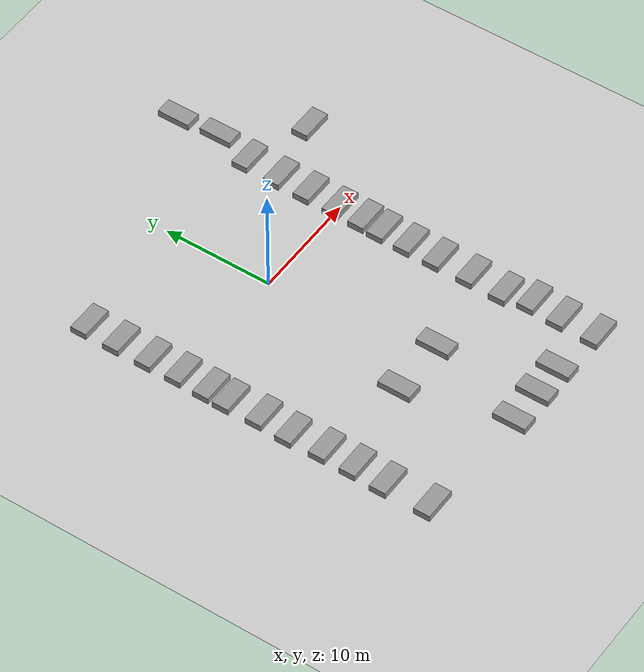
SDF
<sdf version="1.7">
 <world name="default">
  <light name="sun" type="directional">
   <pose>0 0 10 0 -0 0</pose>
   <diffuse>0.8 0.8 0.8 1</diffuse>
   <specular>0.2 0.2 0.2 1</specular>
   <attenuation>
    <range>1000</range>
    <constant>0.9</constant>
    <linear>0.01</linear>
    <quadratic>0.001</quadratic>
   </attenuation>
   <direction>-0.5 0.1 -0.9</direction>
   <spot><inner_angle>0</inner_angle><outer_angle>0</outer_angle><falloff>0</falloff></spot>
  </light>
  <model name="ground_plane">
   <static>1</static>
   <link name="link">
    <collision name="collision">
     <geometry><plane><normal>0 0 1</normal><size>100 100</size></plane></geometry>
     <surface><friction><ode><mu>100</mu><mu2>50</mu2></ode></friction></surface>
    </collision>
    <visual name="visual">
     <cast_shadows>0</cast_shadows>
     <geometry><plane><normal>0 0 1</normal><size>100 100</size></plane></geometry>
     <material>
      <script><uri>file://media/materials/scripts/gazebo.material</uri><name>Gazebo/Grey</name></script>
     </material>
    </visual>
   </link>
  </model>
  <gravity>0 0 -9.8</gravity>
  <magnetic_field>6e-06 2.3e-05 -4.2e-05</magnetic_field>
  <atmosphere type="adiabatic"/>
  <physics type="ode">
   <max_step_size>0.001</max_step_size>
   <real_time_factor>1</real_time_factor>
   <real_time_update_rate>1000</real_time_update_rate>
  </physics>
  <scene><ambient>0.4 0.4 0.4 1</ambient><background>0.7 0.7 0.7 1</background><shadows>1</shadows></scene>
  <audio><device>default</device></audio>
  <spherical_coordinates>
   <surface_model>EARTH_WGS84</surface_model>
   <latitude_deg>0</latitude_deg>
   <longitude_deg>0</longitude_deg>
   <elevation>0</elevation>
   <heading_deg>0</heading_deg>
  </spherical_coordinates>
  <model name="bed_clone">
   <link name="link_2">
    <inertial>
     <mass>1</mass>
     <inertia>
      <ixx>0.166667</ixx>
      <ixy>0</ixy>
      <ixz>0</ixz>
      <iyy>0.166667</iyy>
      <iyz>0</iyz>
      <izz>0.166667</izz>
     </inertia>
    </inertial>
    <pose>-1.5718 2.2064 0 0 -0 0</pose>
    <visual name="visual">
     <geometry><box><size>3 1.5 0.6</size></box></geometry>
     <material>
      <lighting>1</lighting>
      <script><uri>file://media/materials/scripts/gazebo.material</uri><name>Gazebo/Grey</name></script>
      <shader type="pixel"><normal_map>__default__</normal_map></shader>
      <ambient>0.3 0.3 0.3 1</ambient>
      <diffuse>0.7 0.7 0.7 1</diffuse>
      <specular>0.01 0.01 0.01 1</specular>
      <emissive>0 0 0 1</emissive>
     </material>
    </visual>
    <collision name="collision">
     <geometry><box><size>1 1 1</size></box></geometry>
     <surface>
      <friction>
       <ode><mu>1</mu><mu2>1</mu2><fdir1>0 0 0</fdir1><slip1>0</slip1><slip2>0</slip2></ode>
       <torsional>
        <coefficient>1</coefficient>
        <patch_radius>0</patch_radius>
        <surface_radius>0</surface_radius>
        <use_patch_radius>1</use_patch_radius>
        <ode><slip>0</slip></ode>
       </torsional>
      </friction>
      <bounce><restitution_coefficient>0</restitution_coefficient><threshold>1e+06</threshold></bounce>
      <contact>
       <collide_without_contact>0</collide_without_contact>
       <collide_without_contact_bitmask>1</collide_without_contact_bitmask>
       <collide_bitmask>1</collide_bitmask>
       <ode>
        <soft_cfm>0</soft_cfm>
        <soft_erp>0.2</soft_erp>
        <kp>1e+13</kp>
        <kd>1</kd>
        <max_vel>0.01</max_vel>
        <min_depth>0</min_depth>
       </ode>
       <bullet>
        <split_impulse>1</split_impulse>
        <split_impulse_penetration_threshold>-0.01</split_impulse_penetration_threshold>
        <soft_cfm>0</soft_cfm>
        <soft_erp>0.2</soft_erp>
        <kp>1e+13</kp>
        <kd>1</kd>
       </bullet>
      </contact>
     </surface>
    </collision>
   </link>
   <static>0</static>
   <pose>11.5986 3.57422 0.49998 0 1e-05 0</pose>
  </model>
  <model name="bed_clone_0">
   <link name="link_2">
    <inertial>
     <mass>1</mass>
     <inertia>
      <ixx>0.166667</ixx>
      <ixy>0</ixy>
      <ixz>0</ixz>
      <iyy>0.166667</iyy>
      <iyz>0</iyz>
      <izz>0.166667</izz>
     </inertia>
    </inertial>
    <pose>-1.5718 2.2064 0 0 -0 0</pose>
    <visual name="visual">
     <geometry><box><size>3 1.5 0.6</size></box></geometry>
     <material>
      <lighting>1</lighting>
      <script><uri>file://media/materials/scripts/gazebo.material</uri><name>Gazebo/Grey</name></script>
      <shader type="pixel"><normal_map>__default__</normal_map></shader>
      <ambient>0.3 0.3 0.3 1</ambient>
      <diffuse>0.7 0.7 0.7 1</diffuse>
      <specular>0.01 0.01 0.01 1</specular>
      <emissive>0 0 0 1</emissive>
     </material>
    </visual>
    <collision name="collision">
     <geometry><box><size>1 1 1</size></box></geometry>
     <surface>
      <friction>
       <ode><mu>1</mu><mu2>1</mu2><fdir1>0 0 0</fdir1><slip1>0</slip1><slip2>0</slip2></ode>
       <torsional>
        <coefficient>1</coefficient>
        <patch_radius>0</patch_radius>
        <surface_radius>0</surface_radius>
        <use_patch_radius>1</use_patch_radius>
        <ode><slip>0</slip></ode>
       </torsional>
      </friction>
      <bounce><restitution_coefficient>0</restitution_coefficient><threshold>1e+06</threshold></bounce>
      <contact>
       <collide_without_contact>0</collide_without_contact>
       <collide_without_contact_bitmask>1</collide_without_contact_bitmask>
       <collide_bitmask>1</collide_bitmask>
       <ode>
        <soft_cfm>0</soft_cfm>
        <soft_erp>0.2</soft_erp>
        <kp>1e+13</kp>
        <kd>1</kd>
        <max_vel>0.01</max_vel>
        <min_depth>0</min_depth>
       </ode>
       <bullet>
        <split_impulse>1</split_impulse>
        <split_impulse_penetration_threshold>-0.01</split_impulse_penetration_threshold>
        <soft_cfm>0</soft_cfm>
        <soft_erp>0.2</soft_erp>
        <kp>1e+13</kp>
        <kd>1</kd>
       </bullet>
      </contact>
     </surface>
    </collision>
   </link>
   <static>0</static>
   <pose>11.6001 0.66201 0.499974 1e-05 -0 0</pose>
  </model>
  <model name="bed_clone_1">
   <link name="link_2">
    <inertial>
     <mass>1</mass>
     <inertia>
      <ixx>0.166667</ixx>
      <ixy>0</ixy>
      <ixz>0</ixz>
      <iyy>0.166667</iyy>
      <iyz>0</iyz>
      <izz>0.166667</izz>
     </inertia>
    </inertial>
    <pose>-1.5718 2.2064 0 0 -0 0</pose>
    <visual name="visual">
     <geometry><box><size>3 1.5 0.6</size></box></geometry>
     <material>
      <lighting>1</lighting>
      <script><uri>file://media/materials/scripts/gazebo.material</uri><name>Gazebo/Grey</name></script>
      <shader type="pixel"><normal_map>__default__</normal_map></shader>
      <ambient>0.3 0.3 0.3 1</ambient>
      <diffuse>0.7 0.7 0.7 1</diffuse>
      <specular>0.01 0.01 0.01 1</specular>
      <emissive>0 0 0 1</emissive>
     </material>
    </visual>
    <collision name="collision">
     <geometry><box><size>1 1 1</size></box></geometry>
     <surface>
      <friction>
       <ode><mu>1</mu><mu2>1</mu2><fdir1>0 0 0</fdir1><slip1>0</slip1><slip2>0</slip2></ode>
       <torsional>
        <coefficient>1</coefficient>
        <patch_radius>0</patch_radius>
        <surface_radius>0</surface_radius>
        <use_patch_radius>1</use_patch_radius>
        <ode><slip>0</slip></ode>
       </torsional>
      </friction>
      <bounce><restitution_coefficient>0</restitution_coefficient><threshold>1e+06</threshold></bounce>
      <contact>
       <collide_without_contact>0</collide_without_contact>
       <collide_without_contact_bitmask>1</collide_without_contact_bitmask>
       <collide_bitmask>1</collide_bitmask>
       <ode>
        <soft_cfm>0</soft_cfm>
        <soft_erp>0.2</soft_erp>
        <kp>1e+13</kp>
        <kd>1</kd>
        <max_vel>0.01</max_vel>
        <min_depth>0</min_depth>
       </ode>
       <bullet>
        <split_impulse>1</split_impulse>
        <split_impulse_penetration_threshold>-0.01</split_impulse_penetration_threshold>
        <soft_cfm>0</soft_cfm>
        <soft_erp>0.2</soft_erp>
        <kp>1e+13</kp>
        <kd>1</kd>
       </bullet>
      </contact>
     </surface>
    </collision>
   </link>
   <static>0</static>
   <pose>11.5519 -2.19727 0.499974 1e-05 -0 0</pose>
  </model>
  <model name="bed_clone_2">
   <link name="link_2">
    <inertial>
     <mass>1</mass>
     <inertia>
      <ixx>0.166667</ixx>
      <ixy>0</ixy>
      <ixz>0</ixz>
      <iyy>0.166667</iyy>
      <iyz>0</iyz>
      <izz>0.166667</izz>
     </inertia>
    </inertial>
    <pose>-1.5718 2.2064 0 0 -0 0</pose>
    <visual name="visual">
     <geometry><box><size>3 1.5 0.6</size></box></geometry>
     <material>
      <lighting>1</lighting>
      <script><uri>file://media/materials/scripts/gazebo.material</uri><name>Gazebo/Grey</name></script>
      <shader type="pixel"><normal_map>__default__</normal_map></shader>
      <ambient>0.3 0.3 0.3 1</ambient>
      <diffuse>0.7 0.7 0.7 1</diffuse>
      <specular>0.01 0.01 0.01 1</specular>
      <emissive>0 0 0 1</emissive>
     </material>
    </visual>
    <collision name="collision">
     <geometry><box><size>1 1 1</size></box></geometry>
     <surface>
      <friction>
       <ode><mu>1</mu><mu2>1</mu2><fdir1>0 0 0</fdir1><slip1>0</slip1><slip2>0</slip2></ode>
       <torsional>
        <coefficient>1</coefficient>
        <patch_radius>0</patch_radius>
        <surface_radius>0</surface_radius>
        <use_patch_radius>1</use_patch_radius>
        <ode><slip>0</slip></ode>
       </torsional>
      </friction>
      <bounce><restitution_coefficient>0</restitution_coefficient><threshold>1e+06</threshold></bounce>
      <contact>
       <collide_without_contact>0</collide_without_contact>
       <collide_without_contact_bitmask>1</collide_without_contact_bitmask>
       <collide_bitmask>1</collide_bitmask>
       <ode>
        <soft_cfm>0</soft_cfm>
        <soft_erp>0.2</soft_erp>
        <kp>1e+13</kp>
        <kd>1</kd>
        <max_vel>0.01</max_vel>
        <min_depth>0</min_depth>
       </ode>
       <bullet>
        <split_impulse>1</split_impulse>
        <split_impulse_penetration_threshold>-0.01</split_impulse_penetration_threshold>
        <soft_cfm>0</soft_cfm>
        <soft_erp>0.2</soft_erp>
        <kp>1e+13</kp>
        <kd>1</kd>
       </bullet>
      </contact>
     </surface>
    </collision>
   </link>
   <static>0</static>
   <pose>11.5497 -4.68221 0.499974 1e-05 -0 0</pose>
  </model>
  <model name="bed_1_clone_0_clone">
   <link name="link_2">
    <inertial>
     <mass>1</mass>
     <inertia>
      <ixx>0.166667</ixx>
      <ixy>0</ixy>
      <ixz>0</ixz>
      <iyy>0.166667</iyy>
      <iyz>0</iyz>
      <izz>0.166667</izz>
     </inertia>
    </inertial>
    <pose>-1.5718 2.2064 -0 0 -0 0</pose>
    <visual name="visual">
     <geometry><box><size>3 1.5 0.6</size></box></geometry>
     <material>
      <lighting>1</lighting>
      <script><uri>file://media/materials/scripts/gazebo.material</uri><name>Gazebo/Grey</name></script>
      <shader type="pixel"><normal_map>__default__</normal_map></shader>
      <ambient>0.3 0.3 0.3 1</ambient>
      <diffuse>0.7 0.7 0.7 1</diffuse>
      <specular>0.01 0.01 0.01 1</specular>
      <emissive>0 0 0 1</emissive>
     </material>
    </visual>
    <collision name="collision">
     <geometry><box><size>1 1 1</size></box></geometry>
     <surface>
      <friction>
       <ode><mu>1</mu><mu2>1</mu2><fdir1>0 0 0</fdir1><slip1>0</slip1><slip2>0</slip2></ode>
       <torsional>
        <coefficient>1</coefficient>
        <patch_radius>0</patch_radius>
        <surface_radius>0</surface_radius>
        <use_patch_radius>1</use_patch_radius>
        <ode><slip>0</slip></ode>
       </torsional>
      </friction>
      <bounce><restitution_coefficient>0</restitution_coefficient><threshold>1e+06</threshold></bounce>
      <contact>
       <collide_without_contact>0</collide_without_contact>
       <collide_without_contact_bitmask>1</collide_without_contact_bitmask>
       <collide_bitmask>1</collide_bitmask>
       <ode>
        <soft_cfm>0</soft_cfm>
        <soft_erp>0.2</soft_erp>
        <kp>1e+13</kp>
        <kd>1</kd>
        <max_vel>0.01</max_vel>
        <min_depth>0</min_depth>
       </ode>
       <bullet>
        <split_impulse>1</split_impulse>
        <split_impulse_penetration_threshold>-0.01</split_impulse_penetration_threshold>
        <soft_cfm>0</soft_cfm>
        <soft_erp>0.2</soft_erp>
        <kp>1e+13</kp>
        <kd>1</kd>
       </bullet>
      </contact>
     </surface>
    </collision>
   </link>
   <static>0</static>
   <pose>-9.89961 -4.82603 0.49998 0 1e-05 0.002214</pose>
  </model>
  <model name="bed_1_clone_0_clone_0_clone">
   <link name="link_2">
    <inertial>
     <mass>1</mass>
     <inertia>
      <ixx>0.166667</ixx>
      <ixy>0</ixy>
      <ixz>0</ixz>
      <iyy>0.166667</iyy>
      <iyz>0</iyz>
      <izz>0.166667</izz>
     </inertia>
    </inertial>
    <pose>-1.5718 2.2064 -0 0 -0 0</pose>
    <visual name="visual">
     <geometry><box><size>3 1.5 0.6</size></box></geometry>
     <material>
      <lighting>1</lighting>
      <script><uri>file://media/materials/scripts/gazebo.material</uri><name>Gazebo/Grey</name></script>
      <shader type="pixel"><normal_map>__default__</normal_map></shader>
      <ambient>0.3 0.3 0.3 1</ambient>
      <diffuse>0.7 0.7 0.7 1</diffuse>
      <specular>0.01 0.01 0.01 1</specular>
      <emissive>0 0 0 1</emissive>
     </material>
    </visual>
    <collision name="collision">
     <geometry><box><size>1 1 1</size></box></geometry>
     <surface>
      <friction>
       <ode><mu>1</mu><mu2>1</mu2><fdir1>0 0 0</fdir1><slip1>0</slip1><slip2>0</slip2></ode>
       <torsional>
        <coefficient>1</coefficient>
        <patch_radius>0</patch_radius>
        <surface_radius>0</surface_radius>
        <use_patch_radius>1</use_patch_radius>
        <ode><slip>0</slip></ode>
       </torsional>
      </friction>
      <bounce><restitution_coefficient>0</restitution_coefficient><threshold>1e+06</threshold></bounce>
      <contact>
       <collide_without_contact>0</collide_without_contact>
       <collide_without_contact_bitmask>1</collide_without_contact_bitmask>
       <collide_bitmask>1</collide_bitmask>
       <ode>
        <soft_cfm>0</soft_cfm>
        <soft_erp>0.2</soft_erp>
        <kp>1e+13</kp>
        <kd>1</kd>
        <max_vel>0.01</max_vel>
        <min_depth>0</min_depth>
       </ode>
       <bullet>
        <split_impulse>1</split_impulse>
        <split_impulse_penetration_threshold>-0.01</split_impulse_penetration_threshold>
        <soft_cfm>0</soft_cfm>
        <soft_erp>0.2</soft_erp>
        <kp>1e+13</kp>
        <kd>1</kd>
       </bullet>
      </contact>
     </surface>
    </collision>
   </link>
   <static>0</static>
   <pose>-9.8982 0.75484 0.499974 1e-05 -0 0</pose>
  </model>
  <model name="bed_1_clone_0_clone_0_clone_0">
   <link name="link_2">
    <inertial>
     <mass>1</mass>
     <inertia>
      <ixx>0.166667</ixx>
      <ixy>0</ixy>
      <ixz>0</ixz>
      <iyy>0.166667</iyy>
      <iyz>0</iyz>
      <izz>0.166667</izz>
     </inertia>
    </inertial>
    <pose>-1.5718 2.2064 -0 0 -0 0</pose>
    <visual name="visual">
     <geometry><box><size>3 1.5 0.6</size></box></geometry>
     <material>
      <lighting>1</lighting>
      <script><uri>file://media/materials/scripts/gazebo.material</uri><name>Gazebo/Grey</name></script>
      <shader type="pixel"><normal_map>__default__</normal_map></shader>
      <ambient>0.3 0.3 0.3 1</ambient>
      <diffuse>0.7 0.7 0.7 1</diffuse>
      <specular>0.01 0.01 0.01 1</specular>
      <emissive>0 0 0 1</emissive>
     </material>
    </visual>
    <collision name="collision">
     <geometry><box><size>1 1 1</size></box></geometry>
     <surface>
      <friction>
       <ode><mu>1</mu><mu2>1</mu2><fdir1>0 0 0</fdir1><slip1>0</slip1><slip2>0</slip2></ode>
       <torsional>
        <coefficient>1</coefficient>
        <patch_radius>0</patch_radius>
        <surface_radius>0</surface_radius>
        <use_patch_radius>1</use_patch_radius>
        <ode><slip>0</slip></ode>
       </torsional>
      </friction>
      <bounce><restitution_coefficient>0</restitution_coefficient><threshold>1e+06</threshold></bounce>
      <contact>
       <collide_without_contact>0</collide_without_contact>
       <collide_without_contact_bitmask>1</collide_without_contact_bitmask>
       <collide_bitmask>1</collide_bitmask>
       <ode>
        <soft_cfm>0</soft_cfm>
        <soft_erp>0.2</soft_erp>
        <kp>1e+13</kp>
        <kd>1</kd>
        <max_vel>0.01</max_vel>
        <min_depth>0</min_depth>
       </ode>
       <bullet>
        <split_impulse>1</split_impulse>
        <split_impulse_penetration_threshold>-0.01</split_impulse_penetration_threshold>
        <soft_cfm>0</soft_cfm>
        <soft_erp>0.2</soft_erp>
        <kp>1e+13</kp>
        <kd>1</kd>
       </bullet>
      </contact>
     </surface>
    </collision>
   </link>
   <static>0</static>
   <pose>-9.93629 3.78565 0.49998 0 1e-05 0</pose>
  </model>
  <model name="bed_1_clone_0_clone_0_clone_1">
   <link name="link_2">
    <inertial>
     <mass>1</mass>
     <inertia>
      <ixx>0.166667</ixx>
      <ixy>0</ixy>
      <ixz>0</ixz>
      <iyy>0.166667</iyy>
      <iyz>0</iyz>
      <izz>0.166667</izz>
     </inertia>
    </inertial>
    <pose>-1.5718 2.2064 -0 0 -0 0</pose>
    <visual name="visual">
     <geometry><box><size>3 1.5 0.6</size></box></geometry>
     <material>
      <lighting>1</lighting>
      <script><uri>file://media/materials/scripts/gazebo.material</uri><name>Gazebo/Grey</name></script>
      <shader type="pixel"><normal_map>__default__</normal_map></shader>
      <ambient>0.3 0.3 0.3 1</ambient>
      <diffuse>0.7 0.7 0.7 1</diffuse>
      <specular>0.01 0.01 0.01 1</specular>
      <emissive>0 0 0 1</emissive>
     </material>
    </visual>
    <collision name="collision">
     <geometry><box><size>1 1 1</size></box></geometry>
     <surface>
      <friction>
       <ode><mu>1</mu><mu2>1</mu2><fdir1>0 0 0</fdir1><slip1>0</slip1><slip2>0</slip2></ode>
       <torsional>
        <coefficient>1</coefficient>
        <patch_radius>0</patch_radius>
        <surface_radius>0</surface_radius>
        <use_patch_radius>1</use_patch_radius>
        <ode><slip>0</slip></ode>
       </torsional>
      </friction>
      <bounce><restitution_coefficient>0</restitution_coefficient><threshold>1e+06</threshold></bounce>
      <contact>
       <collide_without_contact>0</collide_without_contact>
       <collide_without_contact_bitmask>1</collide_without_contact_bitmask>
       <collide_bitmask>1</collide_bitmask>
       <ode>
        <soft_cfm>0</soft_cfm>
        <soft_erp>0.2</soft_erp>
        <kp>1e+13</kp>
        <kd>1</kd>
        <max_vel>0.01</max_vel>
        <min_depth>0</min_depth>
       </ode>
       <bullet>
        <split_impulse>1</split_impulse>
        <split_impulse_penetration_threshold>-0.01</split_impulse_penetration_threshold>
        <soft_cfm>0</soft_cfm>
        <soft_erp>0.2</soft_erp>
        <kp>1e+13</kp>
        <kd>1</kd>
       </bullet>
      </contact>
     </surface>
    </collision>
   </link>
   <static>0</static>
   <pose>-9.941 6.87097 0.499974 1e-05 -0 0</pose>
  </model>
  <model name="bed_1_clone_0_clone_clone">
   <link name="link_2">
    <inertial>
     <mass>1</mass>
     <inertia>
      <ixx>0.166667</ixx>
      <ixy>0</ixy>
      <ixz>0</ixz>
      <iyy>0.166667</iyy>
      <iyz>0</iyz>
      <izz>0.166667</izz>
     </inertia>
    </inertial>
    <pose>-1.5718 2.2064 -0 0 -0 0</pose>
    <visual name="visual">
     <geometry><box><size>3 1.5 0.6</size></box></geometry>
     <material>
      <lighting>1</lighting>
      <script><uri>file://media/materials/scripts/gazebo.material</uri><name>Gazebo/Grey</name></script>
      <shader type="pixel"><normal_map>__default__</normal_map></shader>
      <ambient>0.3 0.3 0.3 1</ambient>
      <diffuse>0.7 0.7 0.7 1</diffuse>
      <specular>0.01 0.01 0.01 1</specular>
      <emissive>0 0 0 1</emissive>
     </material>
    </visual>
    <collision name="collision">
     <geometry><box><size>1 1 1</size></box></geometry>
     <surface>
      <friction>
       <ode><mu>1</mu><mu2>1</mu2><fdir1>0 0 0</fdir1><slip1>0</slip1><slip2>0</slip2></ode>
       <torsional>
        <coefficient>1</coefficient>
        <patch_radius>0</patch_radius>
        <surface_radius>0</surface_radius>
        <use_patch_radius>1</use_patch_radius>
        <ode><slip>0</slip></ode>
       </torsional>
      </friction>
      <bounce><restitution_coefficient>0</restitution_coefficient><threshold>1e+06</threshold></bounce>
      <contact>
       <collide_without_contact>0</collide_without_contact>
       <collide_without_contact_bitmask>1</collide_without_contact_bitmask>
       <collide_bitmask>1</collide_bitmask>
       <ode>
        <soft_cfm>0</soft_cfm>
        <soft_erp>0.2</soft_erp>
        <kp>1e+13</kp>
        <kd>1</kd>
        <max_vel>0.01</max_vel>
        <min_depth>0</min_depth>
       </ode>
       <bullet>
        <split_impulse>1</split_impulse>
        <split_impulse_penetration_threshold>-0.01</split_impulse_penetration_threshold>
        <soft_cfm>0</soft_cfm>
        <soft_erp>0.2</soft_erp>
        <kp>1e+13</kp>
        <kd>1</kd>
       </bullet>
      </contact>
     </surface>
    </collision>
   </link>
   <static>0</static>
   <pose>-9.83611 -2.10663 0.49998 0 1e-05 0.002214</pose>
  </model>
  <model name="bed_2">
   <link name="link_2">
    <inertial>
     <mass>1</mass>
     <inertia>
      <ixx>0.166667</ixx>
      <ixy>0</ixy>
      <ixz>0</ixz>
      <iyy>0.166667</iyy>
      <iyz>0</iyz>
      <izz>0.166667</izz>
     </inertia>
    </inertial>
    <pose>-1.5718 2.2064 -0 0 -0 0</pose>
    <visual name="visual">
     <geometry><box><size>3 1.5 0.6</size></box></geometry>
     <material>
      <lighting>1</lighting>
      <script><uri>file://media/materials/scripts/gazebo.material</uri><name>Gazebo/Grey</name></script>
      <shader type="pixel"><normal_map>__default__</normal_map></shader>
      <ambient>0.3 0.3 0.3 1</ambient>
      <diffuse>0.7 0.7 0.7 1</diffuse>
      <specular>0.01 0.01 0.01 1</specular>
      <emissive>0 0 0 1</emissive>
     </material>
    </visual>
    <collision name="collision">
     <geometry><box><size>1 1 1</size></box></geometry>
     <surface>
      <friction>
       <ode><mu>1</mu><mu2>1</mu2><fdir1>0 0 0</fdir1><slip1>0</slip1><slip2>0</slip2></ode>
       <torsional>
        <coefficient>1</coefficient>
        <patch_radius>0</patch_radius>
        <surface_radius>0</surface_radius>
        <use_patch_radius>1</use_patch_radius>
        <ode><slip>0</slip></ode>
       </torsional>
      </friction>
      <bounce><restitution_coefficient>0</restitution_coefficient><threshold>1e+06</threshold></bounce>
      <contact>
       <collide_without_contact>0</collide_without_contact>
       <collide_without_contact_bitmask>1</collide_without_contact_bitmask>
       <collide_bitmask>1</collide_bitmask>
       <ode>
        <soft_cfm>0</soft_cfm>
        <soft_erp>0.2</soft_erp>
        <kp>1e+13</kp>
        <kd>1</kd>
        <max_vel>0.01</max_vel>
        <min_depth>0</min_depth>
       </ode>
       <bullet>
        <split_impulse>1</split_impulse>
        <split_impulse_penetration_threshold>-0.01</split_impulse_penetration_threshold>
        <soft_cfm>0</soft_cfm>
        <soft_erp>0.2</soft_erp>
        <kp>1e+13</kp>
        <kd>1</kd>
       </bullet>
      </contact>
     </surface>
    </collision>
   </link>
   <static>0</static>
   <pose>11.7053 -26.6291 0.499974 1e-05 -0 0</pose>
  </model>
  <model name="bed_2_clone">
   <link name="link_2">
    <inertial>
     <mass>1</mass>
     <inertia>
      <ixx>0.166667</ixx>
      <ixy>0</ixy>
      <ixz>0</ixz>
      <iyy>0.166667</iyy>
      <iyz>0</iyz>
      <izz>0.166667</izz>
     </inertia>
    </inertial>
    <pose>-1.5718 2.2064 -0 0 -0 0</pose>
    <visual name="visual">
     <geometry><box><size>3 1.5 0.6</size></box></geometry>
     <material>
      <lighting>1</lighting>
      <script><uri>file://media/materials/scripts/gazebo.material</uri><name>Gazebo/Grey</name></script>
      <shader type="pixel"><normal_map>__default__</normal_map></shader>
      <ambient>0.3 0.3 0.3 1</ambient>
      <diffuse>0.7 0.7 0.7 1</diffuse>
      <specular>0.01 0.01 0.01 1</specular>
      <emissive>0 0 0 1</emissive>
     </material>
    </visual>
    <collision name="collision">
     <geometry><box><size>1 1 1</size></box></geometry>
     <surface>
      <friction>
       <ode><mu>1</mu><mu2>1</mu2><fdir1>0 0 0</fdir1><slip1>0</slip1><slip2>0</slip2></ode>
       <torsional>
        <coefficient>1</coefficient>
        <patch_radius>0</patch_radius>
        <surface_radius>0</surface_radius>
        <use_patch_radius>1</use_patch_radius>
        <ode><slip>0</slip></ode>
       </torsional>
      </friction>
      <bounce><restitution_coefficient>0</restitution_coefficient><threshold>1e+06</threshold></bounce>
      <contact>
       <collide_without_contact>0</collide_without_contact>
       <collide_without_contact_bitmask>1</collide_without_contact_bitmask>
       <collide_bitmask>1</collide_bitmask>
       <ode>
        <soft_cfm>0</soft_cfm>
        <soft_erp>0.2</soft_erp>
        <kp>1e+13</kp>
        <kd>1</kd>
        <max_vel>0.01</max_vel>
        <min_depth>0</min_depth>
       </ode>
       <bullet>
        <split_impulse>1</split_impulse>
        <split_impulse_penetration_threshold>-0.01</split_impulse_penetration_threshold>
        <soft_cfm>0</soft_cfm>
        <soft_erp>0.2</soft_erp>
        <kp>1e+13</kp>
        <kd>1</kd>
       </bullet>
      </contact>
     </surface>
    </collision>
   </link>
   <static>0</static>
   <pose>11.8847 -20.5755 0.49998 0 1e-05 0</pose>
  </model>
  <model name="bed_2_clone_0">
   <link name="link_2">
    <inertial>
     <mass>1</mass>
     <inertia>
      <ixx>0.166667</ixx>
      <ixy>0</ixy>
      <ixz>0</ixz>
      <iyy>0.166667</iyy>
      <iyz>0</iyz>
      <izz>0.166667</izz>
     </inertia>
    </inertial>
    <pose>-1.5718 2.2064 -0 0 -0 0</pose>
    <visual name="visual">
     <geometry><box><size>3 1.5 0.6</size></box></geometry>
     <material>
      <lighting>1</lighting>
      <script><uri>file://media/materials/scripts/gazebo.material</uri><name>Gazebo/Grey</name></script>
      <shader type="pixel"><normal_map>__default__</normal_map></shader>
      <ambient>0.3 0.3 0.3 1</ambient>
      <diffuse>0.7 0.7 0.7 1</diffuse>
      <specular>0.01 0.01 0.01 1</specular>
      <emissive>0 0 0 1</emissive>
     </material>
    </visual>
    <collision name="collision">
     <geometry><box><size>1 1 1</size></box></geometry>
     <surface>
      <friction>
       <ode><mu>1</mu><mu2>1</mu2><fdir1>0 0 0</fdir1><slip1>0</slip1><slip2>0</slip2></ode>
       <torsional>
        <coefficient>1</coefficient>
        <patch_radius>0</patch_radius>
        <surface_radius>0</surface_radius>
        <use_patch_radius>1</use_patch_radius>
        <ode><slip>0</slip></ode>
       </torsional>
      </friction>
      <bounce><restitution_coefficient>0</restitution_coefficient><threshold>1e+06</threshold></bounce>
      <contact>
       <collide_without_contact>0</collide_without_contact>
       <collide_without_contact_bitmask>1</collide_without_contact_bitmask>
       <collide_bitmask>1</collide_bitmask>
       <ode>
        <soft_cfm>0</soft_cfm>
        <soft_erp>0.2</soft_erp>
        <kp>1e+13</kp>
        <kd>1</kd>
        <max_vel>0.01</max_vel>
        <min_depth>0</min_depth>
       </ode>
       <bullet>
        <split_impulse>1</split_impulse>
        <split_impulse_penetration_threshold>-0.01</split_impulse_penetration_threshold>
        <soft_cfm>0</soft_cfm>
        <soft_erp>0.2</soft_erp>
        <kp>1e+13</kp>
        <kd>1</kd>
       </bullet>
      </contact>
     </surface>
    </collision>
   </link>
   <static>0</static>
   <pose>11.7516 -23.4065 0.499974 1e-05 -0 0</pose>
  </model>
  <model name="bed_2_clone_1">
   <link name="link_2">
    <inertial>
     <mass>1</mass>
     <inertia>
      <ixx>0.166667</ixx>
      <ixy>0</ixy>
      <ixz>0</ixz>
      <iyy>0.166667</iyy>
      <iyz>0</iyz>
      <izz>0.166667</izz>
     </inertia>
    </inertial>
    <pose>-1.5718 2.2064 -0 0 -0 0</pose>
    <visual name="visual">
     <geometry><box><size>3 1.5 0.6</size></box></geometry>
     <material>
      <lighting>1</lighting>
      <script><uri>file://media/materials/scripts/gazebo.material</uri><name>Gazebo/Grey</name></script>
      <shader type="pixel"><normal_map>__default__</normal_map></shader>
      <ambient>0.3 0.3 0.3 1</ambient>
      <diffuse>0.7 0.7 0.7 1</diffuse>
      <specular>0.01 0.01 0.01 1</specular>
      <emissive>0 0 0 1</emissive>
     </material>
    </visual>
    <collision name="collision">
     <geometry><box><size>1 1 1</size></box></geometry>
     <surface>
      <friction>
       <ode><mu>1</mu><mu2>1</mu2><fdir1>0 0 0</fdir1><slip1>0</slip1><slip2>0</slip2></ode>
       <torsional>
        <coefficient>1</coefficient>
        <patch_radius>0</patch_radius>
        <surface_radius>0</surface_radius>
        <use_patch_radius>1</use_patch_radius>
        <ode><slip>0</slip></ode>
       </torsional>
      </friction>
      <bounce><restitution_coefficient>0</restitution_coefficient><threshold>1e+06</threshold></bounce>
      <contact>
       <collide_without_contact>0</collide_without_contact>
       <collide_without_contact_bitmask>1</collide_without_contact_bitmask>
       <collide_bitmask>1</collide_bitmask>
       <ode>
        <soft_cfm>0</soft_cfm>
        <soft_erp>0.2</soft_erp>
        <kp>1e+13</kp>
        <kd>1</kd>
        <max_vel>0.01</max_vel>
        <min_depth>0</min_depth>
       </ode>
       <bullet>
        <split_impulse>1</split_impulse>
        <split_impulse_penetration_threshold>-0.01</split_impulse_penetration_threshold>
        <soft_cfm>0</soft_cfm>
        <soft_erp>0.2</soft_erp>
        <kp>1e+13</kp>
        <kd>1</kd>
       </bullet>
      </contact>
     </surface>
    </collision>
   </link>
   <static>0</static>
   <pose>3.12006 -25.232 0.499974 1e-05 -0 -1.57112</pose>
  </model>
  <model name="bed_2_clone_1_clone">
   <link name="link_2">
    <inertial>
     <mass>1</mass>
     <inertia>
      <ixx>0.166667</ixx>
      <ixy>0</ixy>
      <ixz>0</ixz>
      <iyy>0.166667</iyy>
      <iyz>0</iyz>
      <izz>0.166667</izz>
     </inertia>
    </inertial>
    <pose>-1.5718 2.2064 -0 0 -0 0</pose>
    <visual name="visual">
     <geometry><box><size>3 1.5 0.6</size></box></geometry>
     <material>
      <lighting>1</lighting>
      <script><uri>file://media/materials/scripts/gazebo.material</uri><name>Gazebo/Grey</name></script>
      <shader type="pixel"><normal_map>__default__</normal_map></shader>
      <ambient>0.3 0.3 0.3 1</ambient>
      <diffuse>0.7 0.7 0.7 1</diffuse>
      <specular>0.01 0.01 0.01 1</specular>
      <emissive>0 0 0 1</emissive>
     </material>
    </visual>
    <collision name="collision">
     <geometry><box><size>1 1 1</size></box></geometry>
     <surface>
      <friction>
       <ode><mu>1</mu><mu2>1</mu2><fdir1>0 0 0</fdir1><slip1>0</slip1><slip2>0</slip2></ode>
       <torsional>
        <coefficient>1</coefficient>
        <patch_radius>0</patch_radius>
        <surface_radius>0</surface_radius>
        <use_patch_radius>1</use_patch_radius>
        <ode><slip>0</slip></ode>
       </torsional>
      </friction>
      <bounce><restitution_coefficient>0</restitution_coefficient><threshold>1e+06</threshold></bounce>
      <contact>
       <collide_without_contact>0</collide_without_contact>
       <collide_without_contact_bitmask>1</collide_without_contact_bitmask>
       <collide_bitmask>1</collide_bitmask>
       <ode>
        <soft_cfm>0</soft_cfm>
        <soft_erp>0.2</soft_erp>
        <kp>1e+13</kp>
        <kd>1</kd>
        <max_vel>0.01</max_vel>
        <min_depth>0</min_depth>
       </ode>
       <bullet>
        <split_impulse>1</split_impulse>
        <split_impulse_penetration_threshold>-0.01</split_impulse_penetration_threshold>
        <soft_cfm>0</soft_cfm>
        <soft_erp>0.2</soft_erp>
        <kp>1e+13</kp>
        <kd>1</kd>
       </bullet>
      </contact>
     </surface>
    </collision>
   </link>
   <static>0</static>
   <pose>0.175192 -25.2559 0.499974 1e-05 -0 -1.57112</pose>
  </model>
  <model name="bed_2_clone_1_clone_0">
   <link name="link_2">
    <inertial>
     <mass>1</mass>
     <inertia>
      <ixx>0.166667</ixx>
      <ixy>0</ixy>
      <ixz>0</ixz>
      <iyy>0.166667</iyy>
      <iyz>0</iyz>
      <izz>0.166667</izz>
     </inertia>
    </inertial>
    <pose>-1.5718 2.2064 -0 0 -0 0</pose>
    <visual name="visual">
     <geometry><box><size>3 1.5 0.6</size></box></geometry>
     <material>
      <lighting>1</lighting>
      <script><uri>file://media/materials/scripts/gazebo.material</uri><name>Gazebo/Grey</name></script>
      <shader type="pixel"><normal_map>__default__</normal_map></shader>
      <ambient>0.3 0.3 0.3 1</ambient>
      <diffuse>0.7 0.7 0.7 1</diffuse>
      <specular>0.01 0.01 0.01 1</specular>
      <emissive>0 0 0 1</emissive>
     </material>
    </visual>
    <collision name="collision">
     <geometry><box><size>1 1 1</size></box></geometry>
     <surface>
      <friction>
       <ode><mu>1</mu><mu2>1</mu2><fdir1>0 0 0</fdir1><slip1>0</slip1><slip2>0</slip2></ode>
       <torsional>
        <coefficient>1</coefficient>
        <patch_radius>0</patch_radius>
        <surface_radius>0</surface_radius>
        <use_patch_radius>1</use_patch_radius>
        <ode><slip>0</slip></ode>
       </torsional>
      </friction>
      <bounce><restitution_coefficient>0</restitution_coefficient><threshold>1e+06</threshold></bounce>
      <contact>
       <collide_without_contact>0</collide_without_contact>
       <collide_without_contact_bitmask>1</collide_without_contact_bitmask>
       <collide_bitmask>1</collide_bitmask>
       <ode>
        <soft_cfm>0</soft_cfm>
        <soft_erp>0.2</soft_erp>
        <kp>1e+13</kp>
        <kd>1</kd>
        <max_vel>0.01</max_vel>
        <min_depth>0</min_depth>
       </ode>
       <bullet>
        <split_impulse>1</split_impulse>
        <split_impulse_penetration_threshold>-0.01</split_impulse_penetration_threshold>
        <soft_cfm>0</soft_cfm>
        <soft_erp>0.2</soft_erp>
        <kp>1e+13</kp>
        <kd>1</kd>
       </bullet>
      </contact>
     </surface>
    </collision>
   </link>
   <static>0</static>
   <pose>-3.17206 -25.3005 0.499974 1e-05 -0 -1.57112</pose>
  </model>
  <model name="bed_clone_2_clone">
   <link name="link_2">
    <inertial>
     <mass>1</mass>
     <inertia>
      <ixx>0.166667</ixx>
      <ixy>0</ixy>
      <ixz>0</ixz>
      <iyy>0.166667</iyy>
      <iyz>0</iyz>
      <izz>0.166667</izz>
     </inertia>
    </inertial>
    <pose>-1.5718 2.2064 0 0 -0 0</pose>
    <visual name="visual">
     <geometry><box><size>3 1.5 0.6</size></box></geometry>
     <material>
      <lighting>1</lighting>
      <script><uri>file://media/materials/scripts/gazebo.material</uri><name>Gazebo/Grey</name></script>
      <shader type="pixel"><normal_map>__default__</normal_map></shader>
      <ambient>0.3 0.3 0.3 1</ambient>
      <diffuse>0.7 0.7 0.7 1</diffuse>
      <specular>0.01 0.01 0.01 1</specular>
      <emissive>0 0 0 1</emissive>
     </material>
    </visual>
    <collision name="collision">
     <geometry><box><size>1 1 1</size></box></geometry>
     <surface>
      <friction>
       <ode><mu>1</mu><mu2>1</mu2><fdir1>0 0 0</fdir1><slip1>0</slip1><slip2>0</slip2></ode>
       <torsional>
        <coefficient>1</coefficient>
        <patch_radius>0</patch_radius>
        <surface_radius>0</surface_radius>
        <use_patch_radius>1</use_patch_radius>
        <ode><slip>0</slip></ode>
       </torsional>
      </friction>
      <bounce><restitution_coefficient>0</restitution_coefficient><threshold>1e+06</threshold></bounce>
      <contact>
       <collide_without_contact>0</collide_without_contact>
       <collide_without_contact_bitmask>1</collide_without_contact_bitmask>
       <collide_bitmask>1</collide_bitmask>
       <ode>
        <soft_cfm>0</soft_cfm>
        <soft_erp>0.2</soft_erp>
        <kp>1e+13</kp>
        <kd>1</kd>
        <max_vel>0.01</max_vel>
        <min_depth>0</min_depth>
       </ode>
       <bullet>
        <split_impulse>1</split_impulse>
        <split_impulse_penetration_threshold>-0.01</split_impulse_penetration_threshold>
        <soft_cfm>0</soft_cfm>
        <soft_erp>0.2</soft_erp>
        <kp>1e+13</kp>
        <kd>1</kd>
       </bullet>
      </contact>
     </surface>
    </collision>
   </link>
   <static>0</static>
   <pose>11.4742 -6.55679 0.49998 0 1e-05 0</pose>
  </model>
  <model name="bed_clone_2_clone_0">
   <link name="link_2">
    <inertial>
     <mass>1</mass>
     <inertia>
      <ixx>0.166667</ixx>
      <ixy>0</ixy>
      <ixz>0</ixz>
      <iyy>0.166667</iyy>
      <iyz>0</iyz>
      <izz>0.166667</izz>
     </inertia>
    </inertial>
    <pose>-1.5718 2.2064 0 0 -0 0</pose>
    <visual name="visual">
     <geometry><box><size>3 1.5 0.6</size></box></geometry>
     <material>
      <lighting>1</lighting>
      <script><uri>file://media/materials/scripts/gazebo.material</uri><name>Gazebo/Grey</name></script>
      <shader type="pixel"><normal_map>__default__</normal_map></shader>
      <ambient>0.3 0.3 0.3 1</ambient>
      <diffuse>0.7 0.7 0.7 1</diffuse>
      <specular>0.01 0.01 0.01 1</specular>
      <emissive>0 0 0 1</emissive>
     </material>
    </visual>
    <collision name="collision">
     <geometry><box><size>1 1 1</size></box></geometry>
     <surface>
      <friction>
       <ode><mu>1</mu><mu2>1</mu2><fdir1>0 0 0</fdir1><slip1>0</slip1><slip2>0</slip2></ode>
       <torsional>
        <coefficient>1</coefficient>
        <patch_radius>0</patch_radius>
        <surface_radius>0</surface_radius>
        <use_patch_radius>1</use_patch_radius>
        <ode><slip>0</slip></ode>
       </torsional>
      </friction>
      <bounce><restitution_coefficient>0</restitution_coefficient><threshold>1e+06</threshold></bounce>
      <contact>
       <collide_without_contact>0</collide_without_contact>
       <collide_without_contact_bitmask>1</collide_without_contact_bitmask>
       <collide_bitmask>1</collide_bitmask>
       <ode>
        <soft_cfm>0</soft_cfm>
        <soft_erp>0.2</soft_erp>
        <kp>1e+13</kp>
        <kd>1</kd>
        <max_vel>0.01</max_vel>
        <min_depth>0</min_depth>
       </ode>
       <bullet>
        <split_impulse>1</split_impulse>
        <split_impulse_penetration_threshold>-0.01</split_impulse_penetration_threshold>
        <soft_cfm>0</soft_cfm>
        <soft_erp>0.2</soft_erp>
        <kp>1e+13</kp>
        <kd>1</kd>
       </bullet>
      </contact>
     </surface>
    </collision>
   </link>
   <static>0</static>
   <pose>11.4648 -9.13778 0.499974 1e-05 -0 0</pose>
  </model>
  <model name="bed_clone_2_clone_1">
   <link name="link_2">
    <inertial>
     <mass>1</mass>
     <inertia>
      <ixx>0.166667</ixx>
      <ixy>0</ixy>
      <ixz>0</ixz>
      <iyy>0.166667</iyy>
      <iyz>0</iyz>
      <izz>0.166667</izz>
     </inertia>
    </inertial>
    <pose>-1.5718 2.2064 0 0 -0 0</pose>
    <visual name="visual">
     <geometry><box><size>3 1.5 0.6</size></box></geometry>
     <material>
      <lighting>1</lighting>
      <script><uri>file://media/materials/scripts/gazebo.material</uri><name>Gazebo/Grey</name></script>
      <shader type="pixel"><normal_map>__default__</normal_map></shader>
      <ambient>0.3 0.3 0.3 1</ambient>
      <diffuse>0.7 0.7 0.7 1</diffuse>
      <specular>0.01 0.01 0.01 1</specular>
      <emissive>0 0 0 1</emissive>
     </material>
    </visual>
    <collision name="collision">
     <geometry><box><size>1 1 1</size></box></geometry>
     <surface>
      <friction>
       <ode><mu>1</mu><mu2>1</mu2><fdir1>0 0 0</fdir1><slip1>0</slip1><slip2>0</slip2></ode>
       <torsional>
        <coefficient>1</coefficient>
        <patch_radius>0</patch_radius>
        <surface_radius>0</surface_radius>
        <use_patch_radius>1</use_patch_radius>
        <ode><slip>0</slip></ode>
       </torsional>
      </friction>
      <bounce><restitution_coefficient>0</restitution_coefficient><threshold>1e+06</threshold></bounce>
      <contact>
       <collide_without_contact>0</collide_without_contact>
       <collide_without_contact_bitmask>1</collide_without_contact_bitmask>
       <collide_bitmask>1</collide_bitmask>
       <ode>
        <soft_cfm>0</soft_cfm>
        <soft_erp>0.2</soft_erp>
        <kp>1e+13</kp>
        <kd>1</kd>
        <max_vel>0.01</max_vel>
        <min_depth>0</min_depth>
       </ode>
       <bullet>
        <split_impulse>1</split_impulse>
        <split_impulse_penetration_threshold>-0.01</split_impulse_penetration_threshold>
        <soft_cfm>0</soft_cfm>
        <soft_erp>0.2</soft_erp>
        <kp>1e+13</kp>
        <kd>1</kd>
       </bullet>
      </contact>
     </surface>
    </collision>
   </link>
   <static>0</static>
   <pose>11.4594 -11.9252 0.49998 0 1e-05 0</pose>
  </model>
  <model name="bed_clone_2_clone_2">
   <link name="link_2">
    <inertial>
     <mass>1</mass>
     <inertia>
      <ixx>0.166667</ixx>
      <ixy>0</ixy>
      <ixz>0</ixz>
      <iyy>0.166667</iyy>
      <iyz>0</iyz>
      <izz>0.166667</izz>
     </inertia>
    </inertial>
    <pose>-1.5718 2.2064 0 0 -0 0</pose>
    <visual name="visual">
     <geometry><box><size>3 1.5 0.6</size></box></geometry>
     <material>
      <lighting>1</lighting>
      <script><uri>file://media/materials/scripts/gazebo.material</uri><name>Gazebo/Grey</name></script>
      <shader type="pixel"><normal_map>__default__</normal_map></shader>
      <ambient>0.3 0.3 0.3 1</ambient>
      <diffuse>0.7 0.7 0.7 1</diffuse>
      <specular>0.01 0.01 0.01 1</specular>
      <emissive>0 0 0 1</emissive>
     </material>
    </visual>
    <collision name="collision">
     <geometry><box><size>1 1 1</size></box></geometry>
     <surface>
      <friction>
       <ode><mu>1</mu><mu2>1</mu2><fdir1>0 0 0</fdir1><slip1>0</slip1><slip2>0</slip2></ode>
       <torsional>
        <coefficient>1</coefficient>
        <patch_radius>0</patch_radius>
        <surface_radius>0</surface_radius>
        <use_patch_radius>1</use_patch_radius>
        <ode><slip>0</slip></ode>
       </torsional>
      </friction>
      <bounce><restitution_coefficient>0</restitution_coefficient><threshold>1e+06</threshold></bounce>
      <contact>
       <collide_without_contact>0</collide_without_contact>
       <collide_without_contact_bitmask>1</collide_without_contact_bitmask>
       <collide_bitmask>1</collide_bitmask>
       <ode>
        <soft_cfm>0</soft_cfm>
        <soft_erp>0.2</soft_erp>
        <kp>1e+13</kp>
        <kd>1</kd>
        <max_vel>0.01</max_vel>
        <min_depth>0</min_depth>
       </ode>
       <bullet>
        <split_impulse>1</split_impulse>
        <split_impulse_penetration_threshold>-0.01</split_impulse_penetration_threshold>
        <soft_cfm>0</soft_cfm>
        <soft_erp>0.2</soft_erp>
        <kp>1e+13</kp>
        <kd>1</kd>
       </bullet>
      </contact>
     </surface>
    </collision>
   </link>
   <static>0</static>
   <pose>11.4767 -15.0798 0.499974 1e-05 -0 0</pose>
  </model>
  <model name="bed_clone_2_clone_3">
   <link name="link_2">
    <inertial>
     <mass>1</mass>
     <inertia>
      <ixx>0.166667</ixx>
      <ixy>0</ixy>
      <ixz>0</ixz>
      <iyy>0.166667</iyy>
      <iyz>0</iyz>
      <izz>0.166667</izz>
     </inertia>
    </inertial>
    <pose>-1.5718 2.2064 0 0 -0 0</pose>
    <visual name="visual">
     <geometry><box><size>3 1.5 0.6</size></box></geometry>
     <material>
      <lighting>1</lighting>
      <script><uri>file://media/materials/scripts/gazebo.material</uri><name>Gazebo/Grey</name></script>
      <shader type="pixel"><normal_map>__default__</normal_map></shader>
      <ambient>0.3 0.3 0.3 1</ambient>
      <diffuse>0.7 0.7 0.7 1</diffuse>
      <specular>0.01 0.01 0.01 1</specular>
      <emissive>0 0 0 1</emissive>
     </material>
    </visual>
    <collision name="collision">
     <geometry><box><size>1 1 1</size></box></geometry>
     <surface>
      <friction>
       <ode><mu>1</mu><mu2>1</mu2><fdir1>0 0 0</fdir1><slip1>0</slip1><slip2>0</slip2></ode>
       <torsional>
        <coefficient>1</coefficient>
        <patch_radius>0</patch_radius>
        <surface_radius>0</surface_radius>
        <use_patch_radius>1</use_patch_radius>
        <ode><slip>0</slip></ode>
       </torsional>
      </friction>
      <bounce><restitution_coefficient>0</restitution_coefficient><threshold>1e+06</threshold></bounce>
      <contact>
       <collide_without_contact>0</collide_without_contact>
       <collide_without_contact_bitmask>1</collide_without_contact_bitmask>
       <collide_bitmask>1</collide_bitmask>
       <ode>
        <soft_cfm>0</soft_cfm>
        <soft_erp>0.2</soft_erp>
        <kp>1e+13</kp>
        <kd>1</kd>
        <max_vel>0.01</max_vel>
        <min_depth>0</min_depth>
       </ode>
       <bullet>
        <split_impulse>1</split_impulse>
        <split_impulse_penetration_threshold>-0.01</split_impulse_penetration_threshold>
        <soft_cfm>0</soft_cfm>
        <soft_erp>0.2</soft_erp>
        <kp>1e+13</kp>
        <kd>1</kd>
       </bullet>
      </contact>
     </surface>
    </collision>
   </link>
   <static>0</static>
   <pose>11.4189 -18.2146 0.499974 1e-05 -0 0</pose>
  </model>
  <model name="bed_1_clone_0_clone_clone_0">
   <link name="link_2">
    <inertial>
     <mass>1</mass>
     <inertia>
      <ixx>0.166667</ixx>
      <ixy>0</ixy>
      <ixz>0</ixz>
      <iyy>0.166667</iyy>
      <iyz>0</iyz>
      <izz>0.166667</izz>
     </inertia>
    </inertial>
    <pose>-1.5718 2.2064 -0 0 -0 0</pose>
    <visual name="visual">
     <geometry><box><size>3 1.5 0.6</size></box></geometry>
     <material>
      <lighting>1</lighting>
      <script><uri>file://media/materials/scripts/gazebo.material</uri><name>Gazebo/Grey</name></script>
      <shader type="pixel"><normal_map>__default__</normal_map></shader>
      <ambient>0.3 0.3 0.3 1</ambient>
      <diffuse>0.7 0.7 0.7 1</diffuse>
      <specular>0.01 0.01 0.01 1</specular>
      <emissive>0 0 0 1</emissive>
     </material>
    </visual>
    <collision name="collision">
     <geometry><box><size>1 1 1</size></box></geometry>
     <surface>
      <friction>
       <ode><mu>1</mu><mu2>1</mu2><fdir1>0 0 0</fdir1><slip1>0</slip1><slip2>0</slip2></ode>
       <torsional>
        <coefficient>1</coefficient>
        <patch_radius>0</patch_radius>
        <surface_radius>0</surface_radius>
        <use_patch_radius>1</use_patch_radius>
        <ode><slip>0</slip></ode>
       </torsional>
      </friction>
      <bounce><restitution_coefficient>0</restitution_coefficient><threshold>1e+06</threshold></bounce>
      <contact>
       <collide_without_contact>0</collide_without_contact>
       <collide_without_contact_bitmask>1</collide_without_contact_bitmask>
       <collide_bitmask>1</collide_bitmask>
       <ode>
        <soft_cfm>0</soft_cfm>
        <soft_erp>0.2</soft_erp>
        <kp>1e+13</kp>
        <kd>1</kd>
        <max_vel>0.01</max_vel>
        <min_depth>0</min_depth>
       </ode>
       <bullet>
        <split_impulse>1</split_impulse>
        <split_impulse_penetration_threshold>-0.01</split_impulse_penetration_threshold>
        <soft_cfm>0</soft_cfm>
        <soft_erp>0.2</soft_erp>
        <kp>1e+13</kp>
        <kd>1</kd>
       </bullet>
      </contact>
     </surface>
    </collision>
   </link>
   <static>0</static>
   <pose>-9.94232 -6.73588 0.499974 1e-05 -0 0.002214</pose>
  </model>
  <model name="bed_1_clone_0_clone_clone_1">
   <link name="link_2">
    <inertial>
     <mass>1</mass>
     <inertia>
      <ixx>0.166667</ixx>
      <ixy>0</ixy>
      <ixz>0</ixz>
      <iyy>0.166667</iyy>
      <iyz>0</iyz>
      <izz>0.166667</izz>
     </inertia>
    </inertial>
    <pose>-1.5718 2.2064 -0 0 -0 0</pose>
    <visual name="visual">
     <geometry><box><size>3 1.5 0.6</size></box></geometry>
     <material>
      <lighting>1</lighting>
      <script><uri>file://media/materials/scripts/gazebo.material</uri><name>Gazebo/Grey</name></script>
      <shader type="pixel"><normal_map>__default__</normal_map></shader>
      <ambient>0.3 0.3 0.3 1</ambient>
      <diffuse>0.7 0.7 0.7 1</diffuse>
      <specular>0.01 0.01 0.01 1</specular>
      <emissive>0 0 0 1</emissive>
     </material>
    </visual>
    <collision name="collision">
     <geometry><box><size>1 1 1</size></box></geometry>
     <surface>
      <friction>
       <ode><mu>1</mu><mu2>1</mu2><fdir1>0 0 0</fdir1><slip1>0</slip1><slip2>0</slip2></ode>
       <torsional>
        <coefficient>1</coefficient>
        <patch_radius>0</patch_radius>
        <surface_radius>0</surface_radius>
        <use_patch_radius>1</use_patch_radius>
        <ode><slip>0</slip></ode>
       </torsional>
      </friction>
      <bounce><restitution_coefficient>0</restitution_coefficient><threshold>1e+06</threshold></bounce>
      <contact>
       <collide_without_contact>0</collide_without_contact>
       <collide_without_contact_bitmask>1</collide_without_contact_bitmask>
       <collide_bitmask>1</collide_bitmask>
       <ode>
        <soft_cfm>0</soft_cfm>
        <soft_erp>0.2</soft_erp>
        <kp>1e+13</kp>
        <kd>1</kd>
        <max_vel>0.01</max_vel>
        <min_depth>0</min_depth>
       </ode>
       <bullet>
        <split_impulse>1</split_impulse>
        <split_impulse_penetration_threshold>-0.01</split_impulse_penetration_threshold>
        <soft_cfm>0</soft_cfm>
        <soft_erp>0.2</soft_erp>
        <kp>1e+13</kp>
        <kd>1</kd>
       </bullet>
      </contact>
     </surface>
    </collision>
   </link>
   <static>0</static>
   <pose>-9.83741 -9.76736 0.49998 0 1e-05 0.002214</pose>
  </model>
  <model name="bed_1_clone_0_clone_clone_2">
   <link name="link_2">
    <inertial>
     <mass>1</mass>
     <inertia>
      <ixx>0.166667</ixx>
      <ixy>0</ixy>
      <ixz>0</ixz>
      <iyy>0.166667</iyy>
      <iyz>0</iyz>
      <izz>0.166667</izz>
     </inertia>
    </inertial>
    <pose>-1.5718 2.2064 -0 0 -0 0</pose>
    <visual name="visual">
     <geometry><box><size>3 1.5 0.6</size></box></geometry>
     <material>
      <lighting>1</lighting>
      <script><uri>file://media/materials/scripts/gazebo.material</uri><name>Gazebo/Grey</name></script>
      <shader type="pixel"><normal_map>__default__</normal_map></shader>
      <ambient>0.3 0.3 0.3 1</ambient>
      <diffuse>0.7 0.7 0.7 1</diffuse>
      <specular>0.01 0.01 0.01 1</specular>
      <emissive>0 0 0 1</emissive>
     </material>
    </visual>
    <collision name="collision">
     <geometry><box><size>1 1 1</size></box></geometry>
     <surface>
      <friction>
       <ode><mu>1</mu><mu2>1</mu2><fdir1>0 0 0</fdir1><slip1>0</slip1><slip2>0</slip2></ode>
       <torsional>
        <coefficient>1</coefficient>
        <patch_radius>0</patch_radius>
        <surface_radius>0</surface_radius>
        <use_patch_radius>1</use_patch_radius>
        <ode><slip>0</slip></ode>
       </torsional>
      </friction>
      <bounce><restitution_coefficient>0</restitution_coefficient><threshold>1e+06</threshold></bounce>
      <contact>
       <collide_without_contact>0</collide_without_contact>
       <collide_without_contact_bitmask>1</collide_without_contact_bitmask>
       <collide_bitmask>1</collide_bitmask>
       <ode>
        <soft_cfm>0</soft_cfm>
        <soft_erp>0.2</soft_erp>
        <kp>1e+13</kp>
        <kd>1</kd>
        <max_vel>0.01</max_vel>
        <min_depth>0</min_depth>
       </ode>
       <bullet>
        <split_impulse>1</split_impulse>
        <split_impulse_penetration_threshold>-0.01</split_impulse_penetration_threshold>
        <soft_cfm>0</soft_cfm>
        <soft_erp>0.2</soft_erp>
        <kp>1e+13</kp>
        <kd>1</kd>
       </bullet>
      </contact>
     </surface>
    </collision>
   </link>
   <static>0</static>
   <pose>-9.97392 -12.6188 0.499974 1e-05 -0 0.002214</pose>
  </model>
  <model name="bed_1_clone_0_clone_clone_3">
   <link name="link_2">
    <inertial>
     <mass>1</mass>
     <inertia>
      <ixx>0.166667</ixx>
      <ixy>0</ixy>
      <ixz>0</ixz>
      <iyy>0.166667</iyy>
      <iyz>0</iyz>
      <izz>0.166667</izz>
     </inertia>
    </inertial>
    <pose>-1.5718 2.2064 -0 0 -0 0</pose>
    <visual name="visual">
     <geometry><box><size>3 1.5 0.6</size></box></geometry>
     <material>
      <lighting>1</lighting>
      <script><uri>file://media/materials/scripts/gazebo.material</uri><name>Gazebo/Grey</name></script>
      <shader type="pixel"><normal_map>__default__</normal_map></shader>
      <ambient>0.3 0.3 0.3 1</ambient>
      <diffuse>0.7 0.7 0.7 1</diffuse>
      <specular>0.01 0.01 0.01 1</specular>
      <emissive>0 0 0 1</emissive>
     </material>
    </visual>
    <collision name="collision">
     <geometry><box><size>1 1 1</size></box></geometry>
     <surface>
      <friction>
       <ode><mu>1</mu><mu2>1</mu2><fdir1>0 0 0</fdir1><slip1>0</slip1><slip2>0</slip2></ode>
       <torsional>
        <coefficient>1</coefficient>
        <patch_radius>0</patch_radius>
        <surface_radius>0</surface_radius>
        <use_patch_radius>1</use_patch_radius>
        <ode><slip>0</slip></ode>
       </torsional>
      </friction>
      <bounce><restitution_coefficient>0</restitution_coefficient><threshold>1e+06</threshold></bounce>
      <contact>
       <collide_without_contact>0</collide_without_contact>
       <collide_without_contact_bitmask>1</collide_without_contact_bitmask>
       <collide_bitmask>1</collide_bitmask>
       <ode>
        <soft_cfm>0</soft_cfm>
        <soft_erp>0.2</soft_erp>
        <kp>1e+13</kp>
        <kd>1</kd>
        <max_vel>0.01</max_vel>
        <min_depth>0</min_depth>
       </ode>
       <bullet>
        <split_impulse>1</split_impulse>
        <split_impulse_penetration_threshold>-0.01</split_impulse_penetration_threshold>
        <soft_cfm>0</soft_cfm>
        <soft_erp>0.2</soft_erp>
        <kp>1e+13</kp>
        <kd>1</kd>
       </bullet>
      </contact>
     </surface>
    </collision>
   </link>
   <static>0</static>
   <pose>-9.82561 -15.6623 0.49998 0 1e-05 0.002214</pose>
  </model>
  <model name="bed_1_clone_0_clone_clone_4">
   <link name="link_2">
    <inertial>
     <mass>1</mass>
     <inertia>
      <ixx>0.166667</ixx>
      <ixy>0</ixy>
      <ixz>0</ixz>
      <iyy>0.166667</iyy>
      <iyz>0</iyz>
      <izz>0.166667</izz>
     </inertia>
    </inertial>
    <pose>-1.5718 2.2064 -0 0 -0 0</pose>
    <visual name="visual">
     <geometry><box><size>3 1.5 0.6</size></box></geometry>
     <material>
      <lighting>1</lighting>
      <script><uri>file://media/materials/scripts/gazebo.material</uri><name>Gazebo/Grey</name></script>
      <shader type="pixel"><normal_map>__default__</normal_map></shader>
      <ambient>0.3 0.3 0.3 1</ambient>
      <diffuse>0.7 0.7 0.7 1</diffuse>
      <specular>0.01 0.01 0.01 1</specular>
      <emissive>0 0 0 1</emissive>
     </material>
    </visual>
    <collision name="collision">
     <geometry><box><size>1 1 1</size></box></geometry>
     <surface>
      <friction>
       <ode><mu>1</mu><mu2>1</mu2><fdir1>0 0 0</fdir1><slip1>0</slip1><slip2>0</slip2></ode>
       <torsional>
        <coefficient>1</coefficient>
        <patch_radius>0</patch_radius>
        <surface_radius>0</surface_radius>
        <use_patch_radius>1</use_patch_radius>
        <ode><slip>0</slip></ode>
       </torsional>
      </friction>
      <bounce><restitution_coefficient>0</restitution_coefficient><threshold>1e+06</threshold></bounce>
      <contact>
       <collide_without_contact>0</collide_without_contact>
       <collide_without_contact_bitmask>1</collide_without_contact_bitmask>
       <collide_bitmask>1</collide_bitmask>
       <ode>
        <soft_cfm>0</soft_cfm>
        <soft_erp>0.2</soft_erp>
        <kp>1e+13</kp>
        <kd>1</kd>
        <max_vel>0.01</max_vel>
        <min_depth>0</min_depth>
       </ode>
       <bullet>
        <split_impulse>1</split_impulse>
        <split_impulse_penetration_threshold>-0.01</split_impulse_penetration_threshold>
        <soft_cfm>0</soft_cfm>
        <soft_erp>0.2</soft_erp>
        <kp>1e+13</kp>
        <kd>1</kd>
       </bullet>
      </contact>
     </surface>
    </collision>
   </link>
   <static>0</static>
   <pose>-9.83981 -18.5112 0.49998 0 1e-05 0.002214</pose>
  </model>
  <model name="bed_clone_clone">
   <link name="link_2">
    <inertial>
     <mass>1</mass>
     <inertia>
      <ixx>0.166667</ixx>
      <ixy>0</ixy>
      <ixz>0</ixz>
      <iyy>0.166667</iyy>
      <iyz>0</iyz>
      <izz>0.166667</izz>
     </inertia>
    </inertial>
    <pose>-1.5718 2.2064 0 0 -0 0</pose>
    <visual name="visual">
     <geometry><box><size>3 1.5 0.6</size></box></geometry>
     <material>
      <lighting>1</lighting>
      <script><uri>file://media/materials/scripts/gazebo.material</uri><name>Gazebo/Grey</name></script>
      <shader type="pixel"><normal_map>__default__</normal_map></shader>
      <ambient>0.3 0.3 0.3 1</ambient>
      <diffuse>0.7 0.7 0.7 1</diffuse>
      <specular>0.01 0.01 0.01 1</specular>
      <emissive>0 0 0 1</emissive>
     </material>
    </visual>
    <collision name="collision">
     <geometry><box><size>1 1 1</size></box></geometry>
     <surface>
      <friction>
       <ode><mu>1</mu><mu2>1</mu2><fdir1>0 0 0</fdir1><slip1>0</slip1><slip2>0</slip2></ode>
       <torsional>
        <coefficient>1</coefficient>
        <patch_radius>0</patch_radius>
        <surface_radius>0</surface_radius>
        <use_patch_radius>1</use_patch_radius>
        <ode><slip>0</slip></ode>
       </torsional>
      </friction>
      <bounce><restitution_coefficient>0</restitution_coefficient><threshold>1e+06</threshold></bounce>
      <contact>
       <collide_without_contact>0</collide_without_contact>
       <collide_without_contact_bitmask>1</collide_without_contact_bitmask>
       <collide_bitmask>1</collide_bitmask>
       <ode>
        <soft_cfm>0</soft_cfm>
        <soft_erp>0.2</soft_erp>
        <kp>1e+13</kp>
        <kd>1</kd>
        <max_vel>0.01</max_vel>
        <min_depth>0</min_depth>
       </ode>
       <bullet>
        <split_impulse>1</split_impulse>
        <split_impulse_penetration_threshold>-0.01</split_impulse_penetration_threshold>
        <soft_cfm>0</soft_cfm>
        <soft_erp>0.2</soft_erp>
        <kp>1e+13</kp>
        <kd>1</kd>
       </bullet>
      </contact>
     </surface>
    </collision>
   </link>
   <static>0</static>
   <pose>17.3704 4.80074 0.500017 -1e-05 0 0.001328</pose>
  </model>
  <model name="bed_2_clone_1_clone_clone">
   <link name="link_2">
    <inertial>
     <mass>1</mass>
     <inertia>
      <ixx>0.166667</ixx>
      <ixy>0</ixy>
      <ixz>0</ixz>
      <iyy>0.166667</iyy>
      <iyz>0</iyz>
      <izz>0.166667</izz>
     </inertia>
    </inertial>
    <pose>-1.5718 2.2064 -0 0 -0 0</pose>
    <visual name="visual">
     <geometry><box><size>3 1.5 0.6</size></box></geometry>
     <material>
      <lighting>1</lighting>
      <script><uri>file://media/materials/scripts/gazebo.material</uri><name>Gazebo/Grey</name></script>
      <shader type="pixel"><normal_map>__default__</normal_map></shader>
      <ambient>0.3 0.3 0.3 1</ambient>
      <diffuse>0.7 0.7 0.7 1</diffuse>
      <specular>0.01 0.01 0.01 1</specular>
      <emissive>0 0 0 1</emissive>
     </material>
    </visual>
    <collision name="collision">
     <geometry><box><size>1 1 1</size></box></geometry>
     <surface>
      <friction>
       <ode><mu>1</mu><mu2>1</mu2><fdir1>0 0 0</fdir1><slip1>0</slip1><slip2>0</slip2></ode>
       <torsional>
        <coefficient>1</coefficient>
        <patch_radius>0</patch_radius>
        <surface_radius>0</surface_radius>
        <use_patch_radius>1</use_patch_radius>
        <ode><slip>0</slip></ode>
       </torsional>
      </friction>
      <bounce><restitution_coefficient>0</restitution_coefficient><threshold>1e+06</threshold></bounce>
      <contact>
       <collide_without_contact>0</collide_without_contact>
       <collide_without_contact_bitmask>1</collide_without_contact_bitmask>
       <collide_bitmask>1</collide_bitmask>
       <ode>
        <soft_cfm>0</soft_cfm>
        <soft_erp>0.2</soft_erp>
        <kp>1e+13</kp>
        <kd>1</kd>
        <max_vel>0.01</max_vel>
        <min_depth>0</min_depth>
       </ode>
       <bullet>
        <split_impulse>1</split_impulse>
        <split_impulse_penetration_threshold>-0.01</split_impulse_penetration_threshold>
        <soft_cfm>0</soft_cfm>
        <soft_erp>0.2</soft_erp>
        <kp>1e+13</kp>
        <kd>1</kd>
       </bullet>
      </contact>
     </surface>
    </collision>
   </link>
   <static>0</static>
   <pose>-0.240599 -16.2471 0.500017 -1e-05 0 -1.57112</pose>
  </model>
  <model name="bed_2_clone_1_clone_clone_0">
   <link name="link_2">
    <inertial>
     <mass>1</mass>
     <inertia>
      <ixx>0.166667</ixx>
      <ixy>0</ixy>
      <ixz>0</ixz>
      <iyy>0.166667</iyy>
      <iyz>0</iyz>
      <izz>0.166667</izz>
     </inertia>
    </inertial>
    <pose>-1.5718 2.2064 -0 0 -0 0</pose>
    <visual name="visual">
     <geometry><box><size>3 1.5 0.6</size></box></geometry>
     <material>
      <lighting>1</lighting>
      <script><uri>file://media/materials/scripts/gazebo.material</uri><name>Gazebo/Grey</name></script>
      <shader type="pixel"><normal_map>__default__</normal_map></shader>
      <ambient>0.3 0.3 0.3 1</ambient>
      <diffuse>0.7 0.7 0.7 1</diffuse>
      <specular>0.01 0.01 0.01 1</specular>
      <emissive>0 0 0 1</emissive>
     </material>
    </visual>
    <collision name="collision">
     <geometry><box><size>1 1 1</size></box></geometry>
     <surface>
      <friction>
       <ode><mu>1</mu><mu2>1</mu2><fdir1>0 0 0</fdir1><slip1>0</slip1><slip2>0</slip2></ode>
       <torsional>
        <coefficient>1</coefficient>
        <patch_radius>0</patch_radius>
        <surface_radius>0</surface_radius>
        <use_patch_radius>1</use_patch_radius>
        <ode><slip>0</slip></ode>
       </torsional>
      </friction>
      <bounce><restitution_coefficient>0</restitution_coefficient><threshold>1e+06</threshold></bounce>
      <contact>
       <collide_without_contact>0</collide_without_contact>
       <collide_without_contact_bitmask>1</collide_without_contact_bitmask>
       <collide_bitmask>1</collide_bitmask>
       <ode>
        <soft_cfm>0</soft_cfm>
        <soft_erp>0.2</soft_erp>
        <kp>1e+13</kp>
        <kd>1</kd>
        <max_vel>0.01</max_vel>
        <min_depth>0</min_depth>
       </ode>
       <bullet>
        <split_impulse>1</split_impulse>
        <split_impulse_penetration_threshold>-0.01</split_impulse_penetration_threshold>
        <soft_cfm>0</soft_cfm>
        <soft_erp>0.2</soft_erp>
        <kp>1e+13</kp>
        <kd>1</kd>
       </bullet>
      </contact>
     </surface>
    </collision>
   </link>
   <static>0</static>
   <pose>-5.53991 -16.2175 0.50001 -0 -1e-05 -1.57112</pose>
  </model>
  <model name="bed_clone_clone_0">
   <link name="link_2">
    <inertial>
     <mass>1</mass>
     <inertia>
      <ixx>0.166667</ixx>
      <ixy>0</ixy>
      <ixz>0</ixz>
      <iyy>0.166667</iyy>
      <iyz>0</iyz>
      <izz>0.166667</izz>
     </inertia>
    </inertial>
    <pose>-1.5718 2.2064 0 0 -0 0</pose>
    <visual name="visual">
     <geometry><box><size>3 1.5 0.6</size></box></geometry>
     <material>
      <lighting>1</lighting>
      <script><uri>file://media/materials/scripts/gazebo.material</uri><name>Gazebo/Grey</name></script>
      <shader type="pixel"><normal_map>__default__</normal_map></shader>
      <ambient>0.3 0.3 0.3 1</ambient>
      <diffuse>0.7 0.7 0.7 1</diffuse>
      <specular>0.01 0.01 0.01 1</specular>
      <emissive>0 0 0 1</emissive>
     </material>
    </visual>
    <collision name="collision">
     <geometry><box><size>1 1 1</size></box></geometry>
     <surface>
      <friction>
       <ode><mu>1</mu><mu2>1</mu2><fdir1>0 0 0</fdir1><slip1>0</slip1><slip2>0</slip2></ode>
       <torsional>
        <coefficient>1</coefficient>
        <patch_radius>0</patch_radius>
        <surface_radius>0</surface_radius>
        <use_patch_radius>1</use_patch_radius>
        <ode><slip>0</slip></ode>
       </torsional>
      </friction>
      <bounce><restitution_coefficient>0</restitution_coefficient><threshold>1e+06</threshold></bounce>
      <contact>
       <collide_without_contact>0</collide_without_contact>
       <collide_without_contact_bitmask>1</collide_without_contact_bitmask>
       <collide_bitmask>1</collide_bitmask>
       <ode>
        <soft_cfm>0</soft_cfm>
        <soft_erp>0.2</soft_erp>
        <kp>1e+13</kp>
        <kd>1</kd>
        <max_vel>0.01</max_vel>
        <min_depth>0</min_depth>
       </ode>
       <bullet>
        <split_impulse>1</split_impulse>
        <split_impulse_penetration_threshold>-0.01</split_impulse_penetration_threshold>
        <soft_cfm>0</soft_cfm>
        <soft_erp>0.2</soft_erp>
        <kp>1e+13</kp>
        <kd>1</kd>
       </bullet>
      </contact>
     </surface>
    </collision>
   </link>
   <static>0</static>
   <pose>11.6744 6.75209 0.50001 0 -1e-05 0</pose>
  </model>
  <model name="bed_1_clone_0_clone_clone_4_clone">
   <link name="link_2">
    <inertial>
     <mass>1</mass>
     <inertia>
      <ixx>0.166667</ixx>
      <ixy>0</ixy>
      <ixz>0</ixz>
      <iyy>0.166667</iyy>
      <iyz>0</iyz>
      <izz>0.166667</izz>
     </inertia>
    </inertial>
    <pose>-1.5718 2.2064 -0 0 -0 0</pose>
    <visual name="visual">
     <geometry><box><size>3 1.5 0.6</size></box></geometry>
     <material>
      <lighting>1</lighting>
      <script><uri>file://media/materials/scripts/gazebo.material</uri><name>Gazebo/Grey</name></script>
      <shader type="pixel"><normal_map>__default__</normal_map></shader>
      <ambient>0.3 0.3 0.3 1</ambient>
      <diffuse>0.7 0.7 0.7 1</diffuse>
      <specular>0.01 0.01 0.01 1</specular>
      <emissive>0 0 0 1</emissive>
     </material>
    </visual>
    <collision name="collision">
     <geometry><box><size>1 1 1</size></box></geometry>
     <surface>
      <friction>
       <ode><mu>1</mu><mu2>1</mu2><fdir1>0 0 0</fdir1><slip1>0</slip1><slip2>0</slip2></ode>
       <torsional>
        <coefficient>1</coefficient>
        <patch_radius>0</patch_radius>
        <surface_radius>0</surface_radius>
        <use_patch_radius>1</use_patch_radius>
        <ode><slip>0</slip></ode>
       </torsional>
      </friction>
      <bounce><restitution_coefficient>0</restitution_coefficient><threshold>1e+06</threshold></bounce>
      <contact>
       <collide_without_contact>0</collide_without_contact>
       <collide_without_contact_bitmask>1</collide_without_contact_bitmask>
       <collide_bitmask>1</collide_bitmask>
       <ode>
        <soft_cfm>0</soft_cfm>
        <soft_erp>0.2</soft_erp>
        <kp>1e+13</kp>
        <kd>1</kd>
        <max_vel>0.01</max_vel>
        <min_depth>0</min_depth>
       </ode>
       <bullet>
        <split_impulse>1</split_impulse>
        <split_impulse_penetration_threshold>-0.01</split_impulse_penetration_threshold>
        <soft_cfm>0</soft_cfm>
        <soft_erp>0.2</soft_erp>
        <kp>1e+13</kp>
        <kd>1</kd>
       </bullet>
      </contact>
     </surface>
    </collision>
   </link>
   <static>0</static>
   <pose>-9.88763 -25.3985 0.50001 0 -1e-05 0.002214</pose>
  </model>
  <model name="bed_1_clone_0_clone_clone_4_clone_0">
   <link name="link_2">
    <inertial>
     <mass>1</mass>
     <inertia>
      <ixx>0.166667</ixx>
      <ixy>0</ixy>
      <ixz>0</ixz>
      <iyy>0.166667</iyy>
      <iyz>0</iyz>
      <izz>0.166667</izz>
     </inertia>
    </inertial>
    <pose>-1.5718 2.2064 -0 0 -0 0</pose>
    <visual name="visual">
     <geometry><box><size>3 1.5 0.6</size></box></geometry>
     <material>
      <lighting>1</lighting>
      <script><uri>file://media/materials/scripts/gazebo.material</uri><name>Gazebo/Grey</name></script>
      <shader type="pixel"><normal_map>__default__</normal_map></shader>
      <ambient>0.3 0.3 0.3 1</ambient>
      <diffuse>0.7 0.7 0.7 1</diffuse>
      <specular>0.01 0.01 0.01 1</specular>
      <emissive>0 0 0 1</emissive>
     </material>
    </visual>
    <collision name="collision">
     <geometry><box><size>1 1 1</size></box></geometry>
     <surface>
      <friction>
       <ode><mu>1</mu><mu2>1</mu2><fdir1>0 0 0</fdir1><slip1>0</slip1><slip2>0</slip2></ode>
       <torsional>
        <coefficient>1</coefficient>
        <patch_radius>0</patch_radius>
        <surface_radius>0</surface_radius>
        <use_patch_radius>1</use_patch_radius>
        <ode><slip>0</slip></ode>
       </torsional>
      </friction>
      <bounce><restitution_coefficient>0</restitution_coefficient><threshold>1e+06</threshold></bounce>
      <contact>
       <collide_without_contact>0</collide_without_contact>
       <collide_without_contact_bitmask>1</collide_without_contact_bitmask>
       <collide_bitmask>1</collide_bitmask>
       <ode>
        <soft_cfm>0</soft_cfm>
        <soft_erp>0.2</soft_erp>
        <kp>1e+13</kp>
        <kd>1</kd>
        <max_vel>0.01</max_vel>
        <min_depth>0</min_depth>
       </ode>
       <bullet>
        <split_impulse>1</split_impulse>
        <split_impulse_penetration_threshold>-0.01</split_impulse_penetration_threshold>
        <soft_cfm>0</soft_cfm>
        <soft_erp>0.2</soft_erp>
        <kp>1e+13</kp>
        <kd>1</kd>
       </bullet>
      </contact>
     </surface>
    </collision>
   </link>
   <static>0</static>
   <pose>-9.94562 -21.3916 0.499974 1e-05 -0 0.002214</pose>
  </model>
  <model name="bed_2_clone_1_clone_clone_clone">
   <link name="link_2">
    <inertial>
     <mass>1</mass>
     <inertia>
      <ixx>0.166667</ixx>
      <ixy>0</ixy>
      <ixz>0</ixz>
      <iyy>0.166667</iyy>
      <iyz>0</iyz>
      <izz>0.166667</izz>
     </inertia>
    </inertial>
    <pose>-1.5718 2.2064 -0 0 -0 0</pose>
    <visual name="visual">
     <geometry><box><size>3 1.5 0.6</size></box></geometry>
     <material>
      <lighting>1</lighting>
      <script><uri>file://media/materials/scripts/gazebo.material</uri><name>Gazebo/Grey</name></script>
      <shader type="pixel"><normal_map>__default__</normal_map></shader>
      <ambient>0.3 0.3 0.3 1</ambient>
      <diffuse>0.7 0.7 0.7 1</diffuse>
      <specular>0.01 0.01 0.01 1</specular>
      <emissive>0 0 0 1</emissive>
     </material>
    </visual>
    <collision name="collision">
     <geometry><box><size>1 1 1</size></box></geometry>
     <surface>
      <friction>
       <ode><mu>1</mu><mu2>1</mu2><fdir1>0 0 0</fdir1><slip1>0</slip1><slip2>0</slip2></ode>
       <torsional>
        <coefficient>1</coefficient>
        <patch_radius>0</patch_radius>
        <surface_radius>0</surface_radius>
        <use_patch_radius>1</use_patch_radius>
        <ode><slip>0</slip></ode>
       </torsional>
      </friction>
      <bounce><restitution_coefficient>0</restitution_coefficient><threshold>1e+06</threshold></bounce>
      <contact>
       <collide_without_contact>0</collide_without_contact>
       <collide_without_contact_bitmask>1</collide_without_contact_bitmask>
       <collide_bitmask>1</collide_bitmask>
       <ode>
        <soft_cfm>0</soft_cfm>
        <soft_erp>0.2</soft_erp>
        <kp>1e+13</kp>
        <kd>1</kd>
        <max_vel>0.01</max_vel>
        <min_depth>0</min_depth>
       </ode>
       <bullet>
        <split_impulse>1</split_impulse>
        <split_impulse_penetration_threshold>-0.01</split_impulse_penetration_threshold>
        <soft_cfm>0</soft_cfm>
        <soft_erp>0.2</soft_erp>
        <kp>1e+13</kp>
        <kd>1</kd>
       </bullet>
      </contact>
     </surface>
    </collision>
   </link>
   <static>0</static>
   <pose>8.6535 10.8888 0.49998 0 1e-05 -1.57112</pose>
  </model>
  <model name="bed_2_clone_1_clone_clone_clone_clone">
   <link name="link_2">
    <inertial>
     <mass>1</mass>
     <inertia>
      <ixx>0.166667</ixx>
      <ixy>0</ixy>
      <ixz>0</ixz>
      <iyy>0.166667</iyy>
      <iyz>0</iyz>
      <izz>0.166667</izz>
     </inertia>
    </inertial>
    <pose>-1.5718 2.2064 -0 0 -0 0</pose>
    <visual name="visual">
     <geometry><box><size>3 1.5 0.6</size></box></geometry>
     <material>
      <lighting>1</lighting>
      <script><uri>file://media/materials/scripts/gazebo.material</uri><name>Gazebo/Grey</name></script>
      <shader type="pixel"><normal_map>__default__</normal_map></shader>
      <ambient>0.3 0.3 0.3 1</ambient>
      <diffuse>0.7 0.7 0.7 1</diffuse>
      <specular>0.01 0.01 0.01 1</specular>
      <emissive>0 0 0 1</emissive>
     </material>
    </visual>
    <collision name="collision">
     <geometry><box><size>1 1 1</size></box></geometry>
     <surface>
      <friction>
       <ode><mu>1</mu><mu2>1</mu2><fdir1>0 0 0</fdir1><slip1>0</slip1><slip2>0</slip2></ode>
       <torsional>
        <coefficient>1</coefficient>
        <patch_radius>0</patch_radius>
        <surface_radius>0</surface_radius>
        <use_patch_radius>1</use_patch_radius>
        <ode><slip>0</slip></ode>
       </torsional>
      </friction>
      <bounce><restitution_coefficient>0</restitution_coefficient><threshold>1e+06</threshold></bounce>
      <contact>
       <collide_without_contact>0</collide_without_contact>
       <collide_without_contact_bitmask>1</collide_without_contact_bitmask>
       <collide_bitmask>1</collide_bitmask>
       <ode>
        <soft_cfm>0</soft_cfm>
        <soft_erp>0.2</soft_erp>
        <kp>1e+13</kp>
        <kd>1</kd>
        <max_vel>0.01</max_vel>
        <min_depth>0</min_depth>
       </ode>
       <bullet>
        <split_impulse>1</split_impulse>
        <split_impulse_penetration_threshold>-0.01</split_impulse_penetration_threshold>
        <soft_cfm>0</soft_cfm>
        <soft_erp>0.2</soft_erp>
        <kp>1e+13</kp>
        <kd>1</kd>
       </bullet>
      </contact>
     </surface>
    </collision>
   </link>
   <static>0</static>
   <pose>8.35682 14.8375 0.500017 -1e-05 0 -1.57112</pose>
  </model>
 </world>
</sdf>
